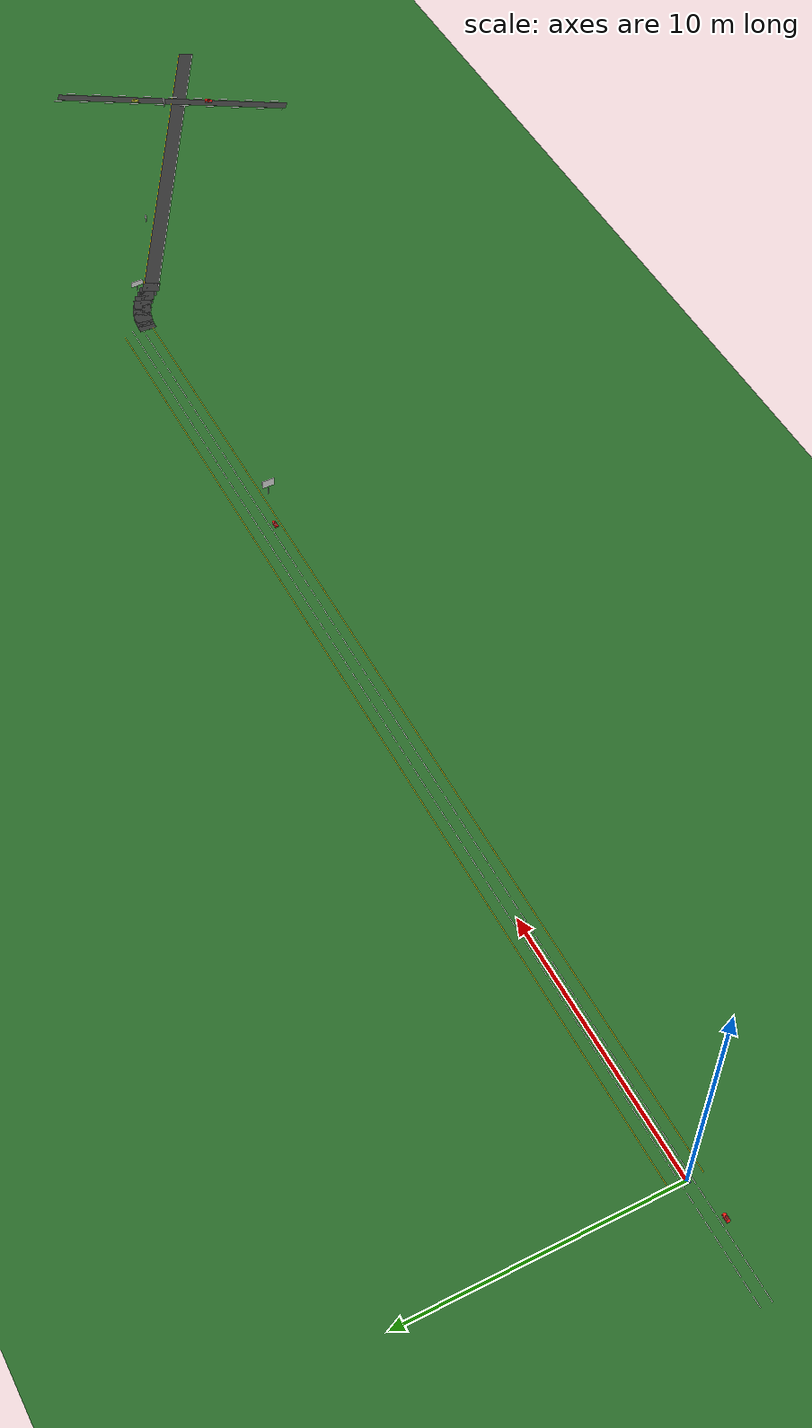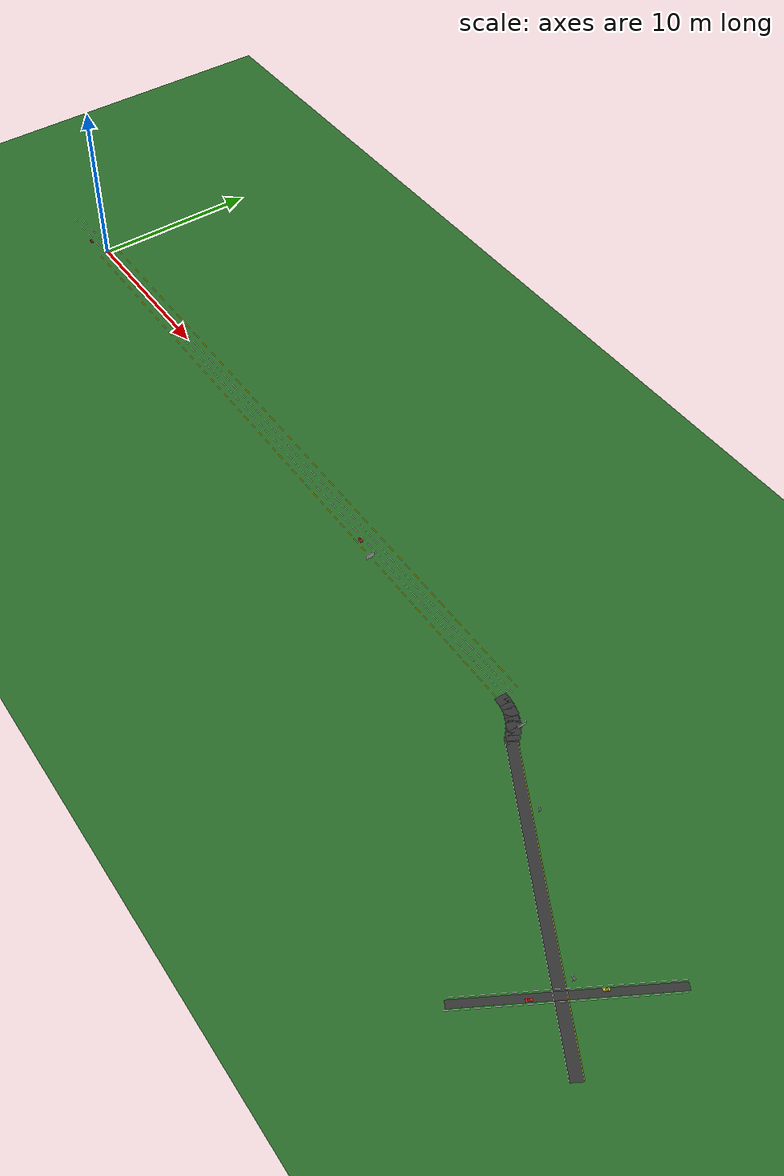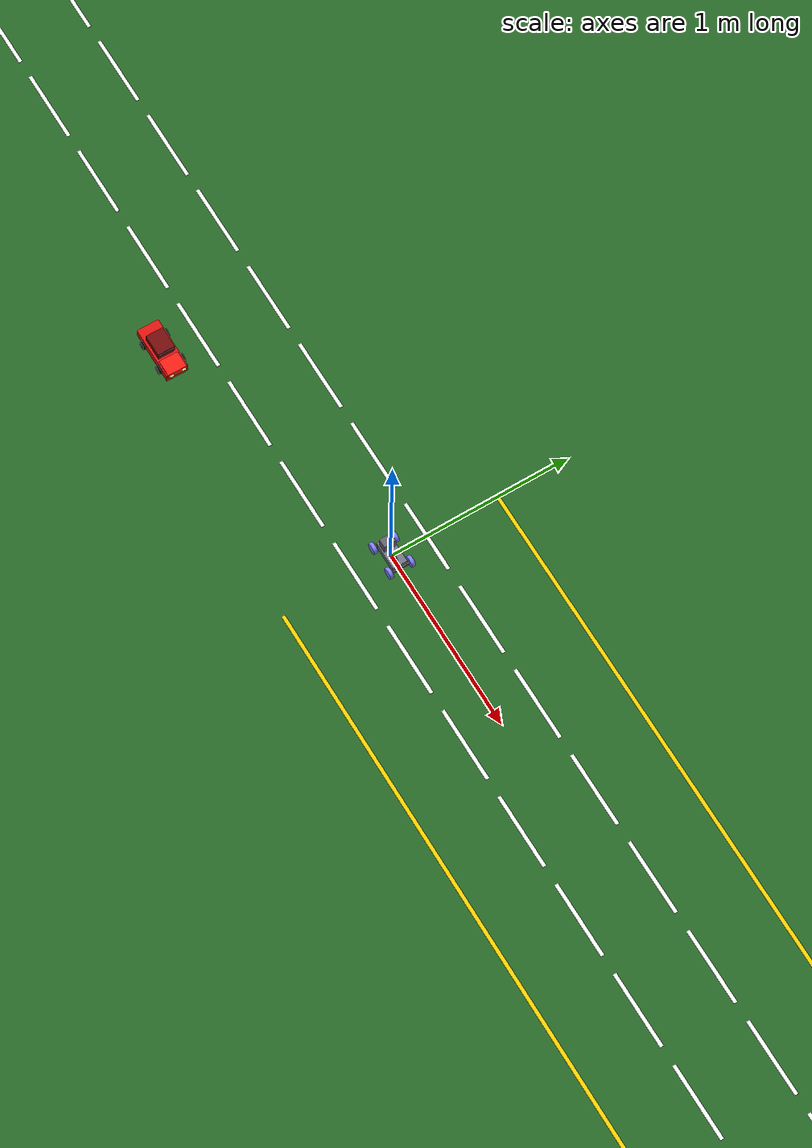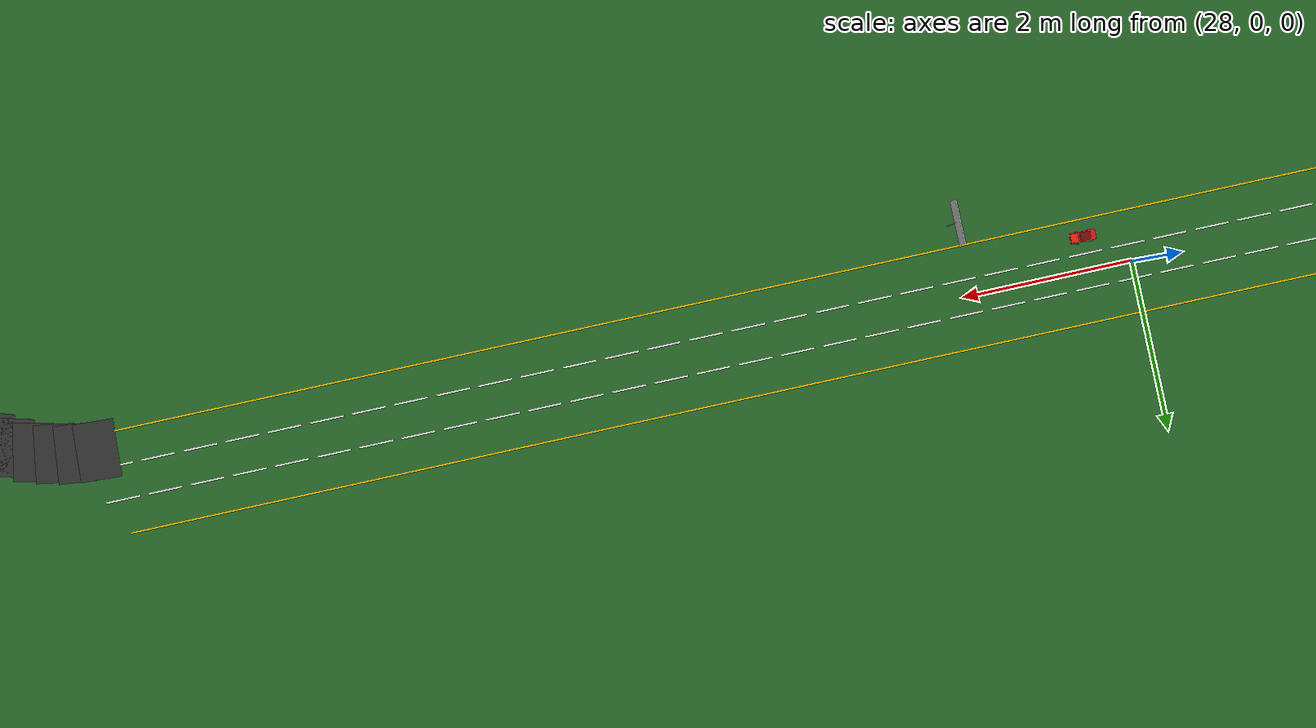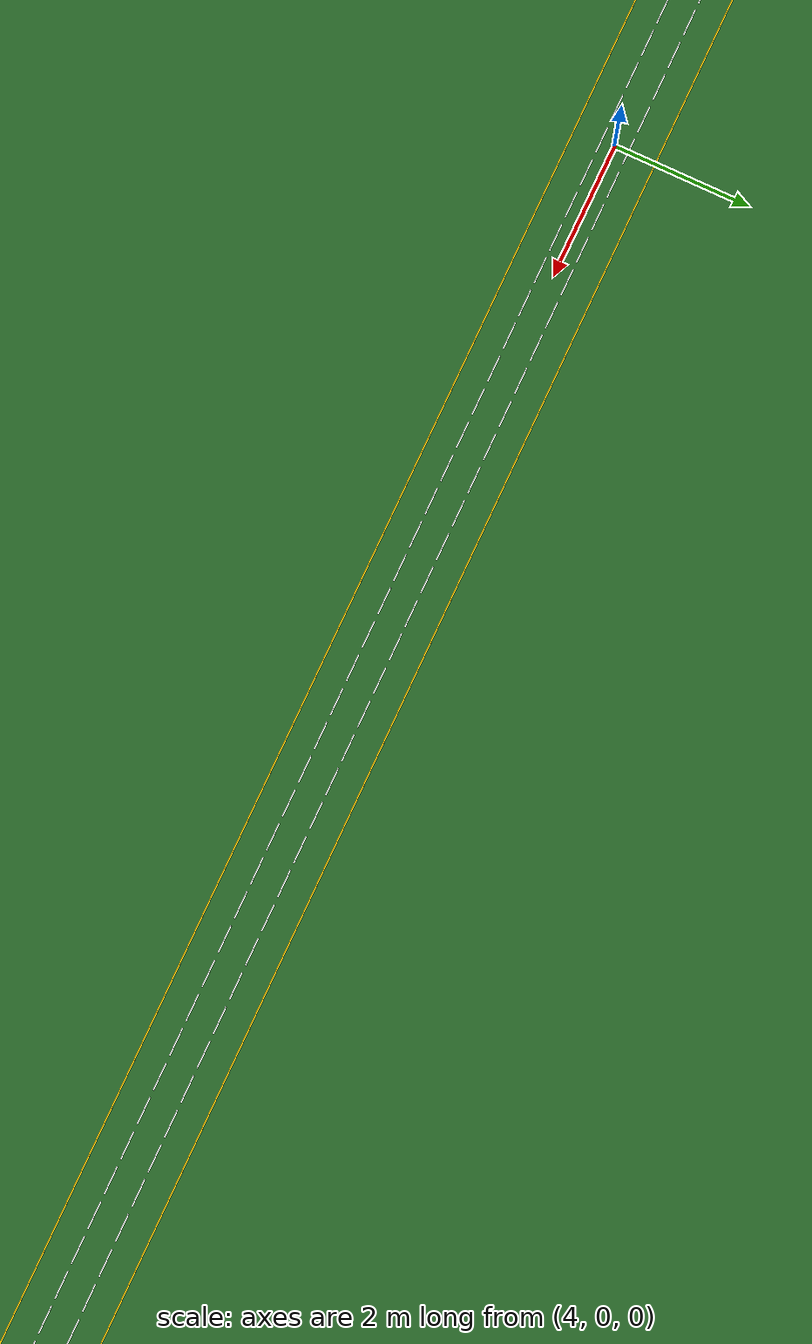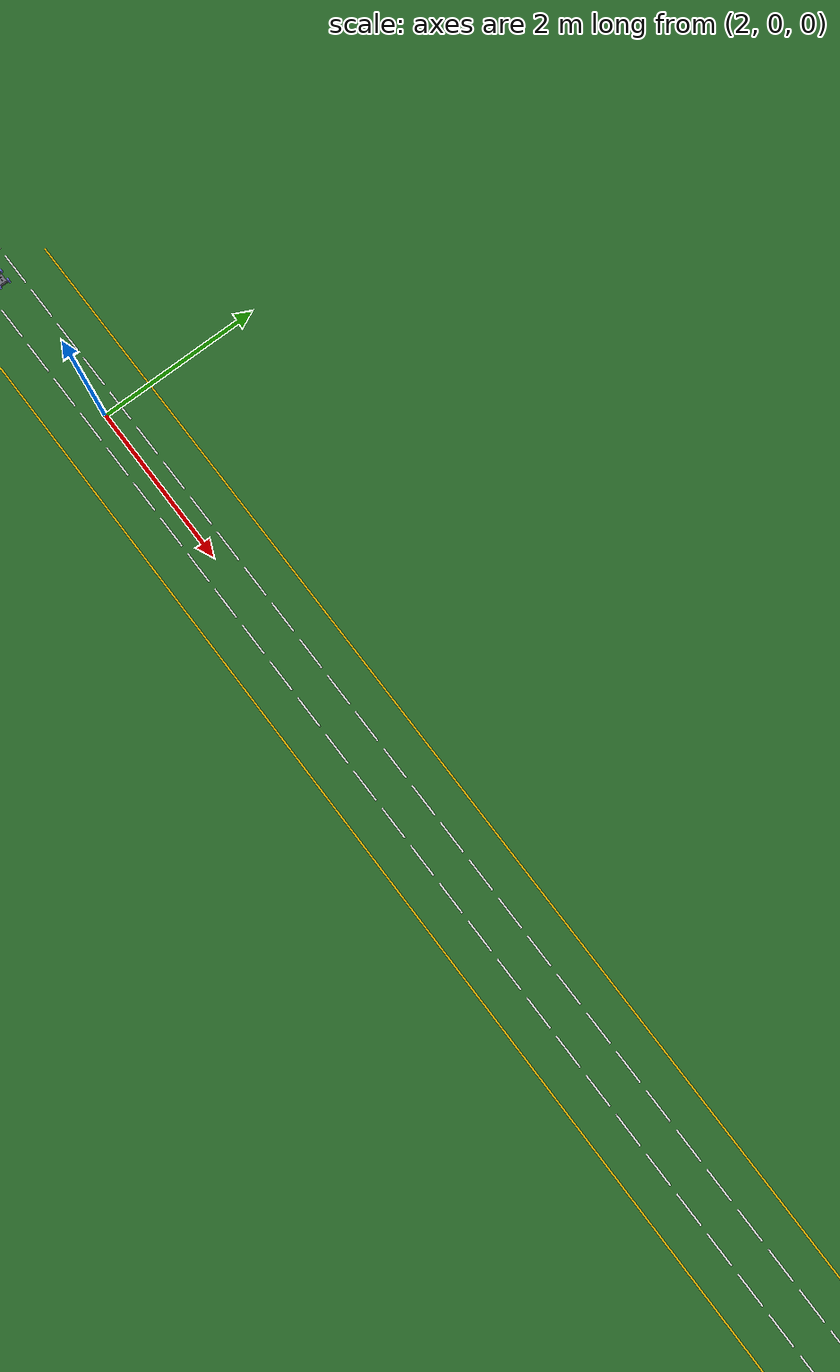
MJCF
<mujoco>
  <compiler autolimits="true"/>

  <!-- Setting to adjust camera/mouse sensitivity to match the car's scale.
       Prevents the massive camera jump on mouse scroll since the initial track was huge. -->
  <statistic extent="3.0" center="0 0 0"/>

  <asset>
      <texture name="grid" type="2d" builtin="checker" width="512" height="512" rgb1=".1 .2 .3" rgb2=".2 .3 .4"/>
      <material name="grid" texture="grid" texrepeat="1 1" texuniform="true" reflectance=".2"/>

    <!-- Sign textures (paths relative to this XML file directory) -->
      <texture name="exit_sign_tex" type="2d" file="exitsign.png"/>
      <material name="exit_sign_mat" texture="exit_sign_tex" texrepeat="1 1" texuniform="true" emission="0.35"/>

      <texture name="lane_change_sign_tex" type="2d" file="lanechange.png"/>
      <material name="lane_change_sign_mat" texture="lane_change_sign_tex" texrepeat="1 1" texuniform="true" emission="0.35"/>

      <texture name="speed_limit_sign_tex" type="2d" file="speed_limit.png"/>
      <material name="speed_limit_sign_mat" texture="speed_limit_sign_tex" texrepeat="1 1" texuniform="true" emission="0.35"/>

      <texture name="stop_sign_tex" type="2d" file="stopsign.png"/>
      <material name="stop_sign_mat" texture="stop_sign_tex" texrepeat="1 1" texuniform="true" emission="0.35"/>
  </asset>

  <default>
    <joint damping=".03" />
    <default class="wheel">
      <geom type="cylinder" size=".03 .01" rgba=".5 .5 1 1"/>
    </default>
    <!-- Steer knuckle joint: larger force range so position actuator can hold angle -->
    <default class="steer">
      <joint type="hinge" axis="0 0 1" range="-0.6 0.6" damping="0.1" actuatorfrcrange="-5 5"/>
    </default>
  </default>

  <worldbody>
    <!-- Wide grassy background for the extended 6 km highway segment. -->
    <geom name="grass" type="plane" pos="30 0 -0.01" size="45 20 .01" rgba="0.15 0.4 0.15 1"/>

    <!-- Straight 6 km, 3-lane road. Scale: 1 MuJoCo meter = 100 real meters; lane centers are y=0.25, y=0.0, y=-0.25. -->
    <geom name="road_asphalt" type="plane" pos="30 0 0" size="45 0.60 .01" rgba="0.2 0.2 0.2 1"/>

    <!-- White dashed lane lines (2cm thick, 1.5m dash length, 1.5m gap) -->
    <geom name="dash_-4.0_L" type="box" pos="-4.0 -0.2 0.002" size="0.2 0.01 0.001" rgba="1 1 1 1" contype="0" conaffinity="0"/>
    <geom name="dash_-4.0_R" type="box" pos="-4.0  0.2 0.002" size="0.2 0.01 0.001" rgba="1 1 1 1" contype="0" conaffinity="0"/>
    <geom name="dash_-3.5_L" type="box" pos="-3.5 -0.2 0.002" size="0.2 0.01 0.001" rgba="1 1 1 1" contype="0" conaffinity="0"/>
    <geom name="dash_-3.5_R" type="box" pos="-3.5  0.2 0.002" size="0.2 0.01 0.001" rgba="1 1 1 1" contype="0" conaffinity="0"/>
    <geom name="dash_-3.0_L" type="box" pos="-3.0 -0.2 0.002" size="0.2 0.01 0.001" rgba="1 1 1 1" contype="0" conaffinity="0"/>
    <geom name="dash_-3.0_R" type="box" pos="-3.0  0.2 0.002" size="0.2 0.01 0.001" rgba="1 1 1 1" contype="0" conaffinity="0"/>
    <geom name="dash_-2.5_L" type="box" pos="-2.5 -0.2 0.002" size="0.2 0.01 0.001" rgba="1 1 1 1" contype="0" conaffinity="0"/>
    <geom name="dash_-2.5_R" type="box" pos="-2.5  0.2 0.002" size="0.2 0.01 0.001" rgba="1 1 1 1" contype="0" conaffinity="0"/>
    <geom name="dash_-2.0_L" type="box" pos="-2.0 -0.2 0.002" size="0.2 0.01 0.001" rgba="1 1 1 1" contype="0" conaffinity="0"/>
    <geom name="dash_-2.0_R" type="box" pos="-2.0  0.2 0.002" size="0.2 0.01 0.001" rgba="1 1 1 1" contype="0" conaffinity="0"/>
    <geom name="dash_-1.5_L" type="box" pos="-1.5 -0.2 0.002" size="0.2 0.01 0.001" rgba="1 1 1 1" contype="0" conaffinity="0"/>
    <geom name="dash_-1.5_R" type="box" pos="-1.5  0.2 0.002" size="0.2 0.01 0.001" rgba="1 1 1 1" contype="0" conaffinity="0"/>
    <geom name="dash_-1.0_L" type="box" pos="-1.0 -0.2 0.002" size="0.2 0.01 0.001" rgba="1 1 1 1" contype="0" conaffinity="0"/>
    <geom name="dash_-1.0_R" type="box" pos="-1.0  0.2 0.002" size="0.2 0.01 0.001" rgba="1 1 1 1" contype="0" conaffinity="0"/>
    <geom name="dash_-0.5_L" type="box" pos="-0.5 -0.2 0.002" size="0.2 0.01 0.001" rgba="1 1 1 1" contype="0" conaffinity="0"/>
    <geom name="dash_-0.5_R" type="box" pos="-0.5  0.2 0.002" size="0.2 0.01 0.001" rgba="1 1 1 1" contype="0" conaffinity="0"/>
    <geom name="dash_0.0_L" type="box" pos="0.0 -0.2 0.002" size="0.2 0.01 0.001" rgba="1 1 1 1" contype="0" conaffinity="0"/>
    <geom name="dash_0.0_R" type="box" pos="0.0  0.2 0.002" size="0.2 0.01 0.001" rgba="1 1 1 1" contype="0" conaffinity="0"/>
    <geom name="dash_0.5_L" type="box" pos="0.5 -0.2 0.002" size="0.2 0.01 0.001" rgba="1 1 1 1" contype="0" conaffinity="0"/>
    <geom name="dash_0.5_R" type="box" pos="0.5  0.2 0.002" size="0.2 0.01 0.001" rgba="1 1 1 1" contype="0" conaffinity="0"/>
    <geom name="dash_1.0_L" type="box" pos="1.0 -0.2 0.002" size="0.2 0.01 0.001" rgba="1 1 1 1" contype="0" conaffinity="0"/>
    <geom name="dash_1.0_R" type="box" pos="1.0  0.2 0.002" size="0.2 0.01 0.001" rgba="1 1 1 1" contype="0" conaffinity="0"/>
    <geom name="dash_1.5_L" type="box" pos="1.5 -0.2 0.002" size="0.2 0.01 0.001" rgba="1 1 1 1" contype="0" conaffinity="0"/>
    <geom name="dash_1.5_R" type="box" pos="1.5  0.2 0.002" size="0.2 0.01 0.001" rgba="1 1 1 1" contype="0" conaffinity="0"/>
    <geom name="dash_2.0_L" type="box" pos="2.0 -0.2 0.002" size="0.2 0.01 0.001" rgba="1 1 1 1" contype="0" conaffinity="0"/>
    <geom name="dash_2.0_R" type="box" pos="2.0  0.2 0.002" size="0.2 0.01 0.001" rgba="1 1 1 1" contype="0" conaffinity="0"/>
    <geom name="dash_2.5_L" type="box" pos="2.5 -0.2 0.002" size="0.2 0.01 0.001" rgba="1 1 1 1" contype="0" conaffinity="0"/>
    <geom name="dash_2.5_R" type="box" pos="2.5  0.2 0.002" size="0.2 0.01 0.001" rgba="1 1 1 1" contype="0" conaffinity="0"/>
    <geom name="dash_3.0_L" type="box" pos="3.0 -0.2 0.002" size="0.2 0.01 0.001" rgba="1 1 1 1" contype="0" conaffinity="0"/>
    <geom name="dash_3.0_R" type="box" pos="3.0  0.2 0.002" size="0.2 0.01 0.001" rgba="1 1 1 1" contype="0" conaffinity="0"/>
    <geom name="dash_3.5_L" type="box" pos="3.5 -0.2 0.002" size="0.2 0.01 0.001" rgba="1 1 1 1" contype="0" conaffinity="0"/>
    <geom name="dash_3.5_R" type="box" pos="3.5  0.2 0.002" size="0.2 0.01 0.001" rgba="1 1 1 1" contype="0" conaffinity="0"/>
    <geom name="dash_4.0_L" type="box" pos="4.0 -0.2 0.002" size="0.2 0.01 0.001" rgba="1 1 1 1" contype="0" conaffinity="0"/>
    <geom name="dash_4.0_R" type="box" pos="4.0  0.2 0.002" size="0.2 0.01 0.001" rgba="1 1 1 1" contype="0" conaffinity="0"/>
    <geom name="dash_4.5_L" type="box" pos="4.5 -0.2 0.002" size="0.2 0.01 0.001" rgba="1 1 1 1" contype="0" conaffinity="0"/>
    <geom name="dash_4.5_R" type="box" pos="4.5  0.2 0.002" size="0.2 0.01 0.001" rgba="1 1 1 1" contype="0" conaffinity="0"/>
    <geom name="dash_5.0_L" type="box" pos="5.0 -0.2 0.002" size="0.2 0.01 0.001" rgba="1 1 1 1" contype="0" conaffinity="0"/>
    <geom name="dash_5.0_R" type="box" pos="5.0  0.2 0.002" size="0.2 0.01 0.001" rgba="1 1 1 1" contype="0" conaffinity="0"/>
    <geom name="dash_5.5_L" type="box" pos="5.5 -0.2 0.002" size="0.2 0.01 0.001" rgba="1 1 1 1" contype="0" conaffinity="0"/>
    <geom name="dash_5.5_R" type="box" pos="5.5  0.2 0.002" size="0.2 0.01 0.001" rgba="1 1 1 1" contype="0" conaffinity="0"/>
    <geom name="dash_6.0_L" type="box" pos="6.0 -0.2 0.002" size="0.2 0.01 0.001" rgba="1 1 1 1" contype="0" conaffinity="0"/>
    <geom name="dash_6.0_R" type="box" pos="6.0  0.2 0.002" size="0.2 0.01 0.001" rgba="1 1 1 1" contype="0" conaffinity="0"/>
    <geom name="dash_6.5_L" type="box" pos="6.5 -0.2 0.002" size="0.2 0.01 0.001" rgba="1 1 1 1" contype="0" conaffinity="0"/>
    <geom name="dash_6.5_R" type="box" pos="6.5  0.2 0.002" size="0.2 0.01 0.001" rgba="1 1 1 1" contype="0" conaffinity="0"/>
    <geom name="dash_7.0_L" type="box" pos="7.0 -0.2 0.002" size="0.2 0.01 0.001" rgba="1 1 1 1" contype="0" conaffinity="0"/>
    <geom name="dash_7.0_R" type="box" pos="7.0  0.2 0.002" size="0.2 0.01 0.001" rgba="1 1 1 1" contype="0" conaffinity="0"/>
    <geom name="dash_7.5_L" type="box" pos="7.5 -0.2 0.002" size="0.2 0.01 0.001" rgba="1 1 1 1" contype="0" conaffinity="0"/>
    <geom name="dash_7.5_R" type="box" pos="7.5  0.2 0.002" size="0.2 0.01 0.001" rgba="1 1 1 1" contype="0" conaffinity="0"/>
    <geom name="dash_8.0_L" type="box" pos="8.0 -0.2 0.002" size="0.2 0.01 0.001" rgba="1 1 1 1" contype="0" conaffinity="0"/>
    <geom name="dash_8.0_R" type="box" pos="8.0  0.2 0.002" size="0.2 0.01 0.001" rgba="1 1 1 1" contype="0" conaffinity="0"/>
    <geom name="dash_8.5_L" type="box" pos="8.5 -0.2 0.002" size="0.2 0.01 0.001" rgba="1 1 1 1" contype="0" conaffinity="0"/>
    <geom name="dash_8.5_R" type="box" pos="8.5  0.2 0.002" size="0.2 0.01 0.001" rgba="1 1 1 1" contype="0" conaffinity="0"/>
    <geom name="dash_9.0_L" type="box" pos="9.0 -0.2 0.002" size="0.2 0.01 0.001" rgba="1 1 1 1" contype="0" conaffinity="0"/>
    <geom name="dash_9.0_R" type="box" pos="9.0  0.2 0.002" size="0.2 0.01 0.001" rgba="1 1 1 1" contype="0" conaffinity="0"/>
    <geom name="dash_9.5_L" type="box" pos="9.5 -0.2 0.002" size="0.2 0.01 0.001" rgba="1 1 1 1" contype="0" conaffinity="0"/>
    <geom name="dash_9.5_R" type="box" pos="9.5  0.2 0.002" size="0.2 0.01 0.001" rgba="1 1 1 1" contype="0" conaffinity="0"/>
    <geom name="dash_10.0_L" type="box" pos="10.0 -0.2 0.002" size="0.2 0.01 0.001" rgba="1 1 1 1" contype="0" conaffinity="0"/>
    <geom name="dash_10.0_R" type="box" pos="10.0  0.2 0.002" size="0.2 0.01 0.001" rgba="1 1 1 1" contype="0" conaffinity="0"/>
    <geom name="dash_10.5_L" type="box" pos="10.5 -0.2 0.002" size="0.2 0.01 0.001" rgba="1 1 1 1" contype="0" conaffinity="0"/>
    <geom name="dash_10.5_R" type="box" pos="10.5  0.2 0.002" size="0.2 0.01 0.001" rgba="1 1 1 1" contype="0" conaffinity="0"/>
    <geom name="dash_11.0_L" type="box" pos="11.0 -0.2 0.002" size="0.2 0.01 0.001" rgba="1 1 1 1" contype="0" conaffinity="0"/>
    <geom name="dash_11.0_R" type="box" pos="11.0  0.2 0.002" size="0.2 0.01 0.001" rgba="1 1 1 1" contype="0" conaffinity="0"/>
    <geom name="dash_11.5_L" type="box" pos="11.5 -0.2 0.002" size="0.2 0.01 0.001" rgba="1 1 1 1" contype="0" conaffinity="0"/>
    <geom name="dash_11.5_R" type="box" pos="11.5  0.2 0.002" size="0.2 0.01 0.001" rgba="1 1 1 1" contype="0" conaffinity="0"/>
    <geom name="dash_12.0_L" type="box" pos="12.0 -0.2 0.002" size="0.2 0.01 0.001" rgba="1 1 1 1" contype="0" conaffinity="0"/>
    <geom name="dash_12.0_R" type="box" pos="12.0  0.2 0.002" size="0.2 0.01 0.001" rgba="1 1 1 1" contype="0" conaffinity="0"/>
    <geom name="dash_12.5_L" type="box" pos="12.5 -0.2 0.002" size="0.2 0.01 0.001" rgba="1 1 1 1" contype="0" conaffinity="0"/>
    <geom name="dash_12.5_R" type="box" pos="12.5  0.2 0.002" size="0.2 0.01 0.001" rgba="1 1 1 1" contype="0" conaffinity="0"/>
    <geom name="dash_13.0_L" type="box" pos="13.0 -0.2 0.002" size="0.2 0.01 0.001" rgba="1 1 1 1" contype="0" conaffinity="0"/>
    <geom name="dash_13.0_R" type="box" pos="13.0  0.2 0.002" size="0.2 0.01 0.001" rgba="1 1 1 1" contype="0" conaffinity="0"/>
    <geom name="dash_13.5_L" type="box" pos="13.5 -0.2 0.002" size="0.2 0.01 0.001" rgba="1 1 1 1" contype="0" conaffinity="0"/>
    <geom name="dash_13.5_R" type="box" pos="13.5  0.2 0.002" size="0.2 0.01 0.001" rgba="1 1 1 1" contype="0" conaffinity="0"/>
    <geom name="dash_14.0_L" type="box" pos="14.0 -0.2 0.002" size="0.2 0.01 0.001" rgba="1 1 1 1" contype="0" conaffinity="0"/>
    <geom name="dash_14.0_R" type="box" pos="14.0  0.2 0.002" size="0.2 0.01 0.001" rgba="1 1 1 1" contype="0" conaffinity="0"/>
    <geom name="dash_14.5_L" type="box" pos="14.5 -0.2 0.002" size="0.2 0.01 0.001" rgba="1 1 1 1" contype="0" conaffinity="0"/>
    <geom name="dash_14.5_R" type="box" pos="14.5  0.2 0.002" size="0.2 0.01 0.001" rgba="1 1 1 1" contype="0" conaffinity="0"/>
    <geom name="dash_15.0_L" type="box" pos="15.0 -0.2 0.002" size="0.2 0.01 0.001" rgba="1 1 1 1" contype="0" conaffinity="0"/>
    <geom name="dash_15.0_R" type="box" pos="15.0  0.2 0.002" size="0.2 0.01 0.001" rgba="1 1 1 1" contype="0" conaffinity="0"/>
    <geom name="dash_15.5_L" type="box" pos="15.5 -0.2 0.002" size="0.2 0.01 0.001" rgba="1 1 1 1" contype="0" conaffinity="0"/>
    <geom name="dash_15.5_R" type="box" pos="15.5  0.2 0.002" size="0.2 0.01 0.001" rgba="1 1 1 1" contype="0" conaffinity="0"/>
    <geom name="dash_16.0_L" type="box" pos="16.0 -0.2 0.002" size="0.2 0.01 0.001" rgba="1 1 1 1" contype="0" conaffinity="0"/>
    <geom name="dash_16.0_R" type="box" pos="16.0  0.2 0.002" size="0.2 0.01 0.001" rgba="1 1 1 1" contype="0" conaffinity="0"/>
    <geom name="dash_16.5_L" type="box" pos="16.5 -0.2 0.002" size="0.2 0.01 0.001" rgba="1 1 1 1" contype="0" conaffinity="0"/>
    <geom name="dash_16.5_R" type="box" pos="16.5  0.2 0.002" size="0.2 0.01 0.001" rgba="1 1 1 1" contype="0" conaffinity="0"/>
    <geom name="dash_17.0_L" type="box" pos="17.0 -0.2 0.002" size="0.2 0.01 0.001" rgba="1 1 1 1" contype="0" conaffinity="0"/>
    <geom name="dash_17.0_R" type="box" pos="17.0  0.2 0.002" size="0.2 0.01 0.001" rgba="1 1 1 1" contype="0" conaffinity="0"/>
    <geom name="dash_17.5_L" type="box" pos="17.5 -0.2 0.002" size="0.2 0.01 0.001" rgba="1 1 1 1" contype="0" conaffinity="0"/>
    <geom name="dash_17.5_R" type="box" pos="17.5  0.2 0.002" size="0.2 0.01 0.001" rgba="1 1 1 1" contype="0" conaffinity="0"/>
    <geom name="dash_18.0_L" type="box" pos="18.0 -0.2 0.002" size="0.2 0.01 0.001" rgba="1 1 1 1" contype="0" conaffinity="0"/>
    <geom name="dash_18.0_R" type="box" pos="18.0  0.2 0.002" size="0.2 0.01 0.001" rgba="1 1 1 1" contype="0" conaffinity="0"/>
    <geom name="dash_18.5_L" type="box" pos="18.5 -0.2 0.002" size="0.2 0.01 0.001" rgba="1 1 1 1" contype="0" conaffinity="0"/>
    <geom name="dash_18.5_R" type="box" pos="18.5  0.2 0.002" size="0.2 0.01 0.001" rgba="1 1 1 1" contype="0" conaffinity="0"/>
    <geom name="dash_19.0_L" type="box" pos="19.0 -0.2 0.002" size="0.2 0.01 0.001" rgba="1 1 1 1" contype="0" conaffinity="0"/>
    <geom name="dash_19.0_R" type="box" pos="19.0  0.2 0.002" size="0.2 0.01 0.001" rgba="1 1 1 1" contype="0" conaffinity="0"/>
    <geom name="dash_19.5_L" type="box" pos="19.5 -0.2 0.002" size="0.2 0.01 0.001" rgba="1 1 1 1" contype="0" conaffinity="0"/>
    <geom name="dash_19.5_R" type="box" pos="19.5  0.2 0.002" size="0.2 0.01 0.001" rgba="1 1 1 1" contype="0" conaffinity="0"/>
    <geom name="dash_20.0_L" type="box" pos="20.0 -0.2 0.002" size="0.2 0.01 0.001" rgba="1 1 1 1" contype="0" conaffinity="0"/>
    <geom name="dash_20.0_R" type="box" pos="20.0  0.2 0.002" size="0.2 0.01 0.001" rgba="1 1 1 1" contype="0" conaffinity="0"/>
    <geom name="dash_20.5_L" type="box" pos="20.5 -0.2 0.002" size="0.2 0.01 0.001" rgba="1 1 1 1" contype="0" conaffinity="0"/>
    <geom name="dash_20.5_R" type="box" pos="20.5  0.2 0.002" size="0.2 0.01 0.001" rgba="1 1 1 1" contype="0" conaffinity="0"/>
    <geom name="dash_21.0_L" type="box" pos="21.0 -0.2 0.002" size="0.2 0.01 0.001" rgba="1 1 1 1" contype="0" conaffinity="0"/>
    <geom name="dash_21.0_R" type="box" pos="21.0  0.2 0.002" size="0.2 0.01 0.001" rgba="1 1 1 1" contype="0" conaffinity="0"/>
    <geom name="dash_21.5_L" type="box" pos="21.5 -0.2 0.002" size="0.2 0.01 0.001" rgba="1 1 1 1" contype="0" conaffinity="0"/>
    <geom name="dash_21.5_R" type="box" pos="21.5  0.2 0.002" size="0.2 0.01 0.001" rgba="1 1 1 1" contype="0" conaffinity="0"/>
    <geom name="dash_22.0_L" type="box" pos="22.0 -0.2 0.002" size="0.2 0.01 0.001" rgba="1 1 1 1" contype="0" conaffinity="0"/>
    <geom name="dash_22.0_R" type="box" pos="22.0  0.2 0.002" size="0.2 0.01 0.001" rgba="1 1 1 1" contype="0" conaffinity="0"/>
    <geom name="dash_22.5_L" type="box" pos="22.5 -0.2 0.002" size="0.2 0.01 0.001" rgba="1 1 1 1" contype="0" conaffinity="0"/>
    <geom name="dash_22.5_R" type="box" pos="22.5  0.2 0.002" size="0.2 0.01 0.001" rgba="1 1 1 1" contype="0" conaffinity="0"/>
    <geom name="dash_23.0_L" type="box" pos="23.0 -0.2 0.002" size="0.2 0.01 0.001" rgba="1 1 1 1" contype="0" conaffinity="0"/>
    <geom name="dash_23.0_R" type="box" pos="23.0  0.2 0.002" size="0.2 0.01 0.001" rgba="1 1 1 1" contype="0" conaffinity="0"/>
    <geom name="dash_23.5_L" type="box" pos="23.5 -0.2 0.002" size="0.2 0.01 0.001" rgba="1 1 1 1" contype="0" conaffinity="0"/>
    <geom name="dash_23.5_R" type="box" pos="23.5  0.2 0.002" size="0.2 0.01 0.001" rgba="1 1 1 1" contype="0" conaffinity="0"/>
    <geom name="dash_24.0_L" type="box" pos="24.0 -0.2 0.002" size="0.2 0.01 0.001" rgba="1 1 1 1" contype="0" conaffinity="0"/>
    <geom name="dash_24.0_R" type="box" pos="24.0  0.2 0.002" size="0.2 0.01 0.001" rgba="1 1 1 1" contype="0" conaffinity="0"/>
    <geom name="dash_24.5_L" type="box" pos="24.5 -0.2 0.002" size="0.2 0.01 0.001" rgba="1 1 1 1" contype="0" conaffinity="0"/>
    <geom name="dash_24.5_R" type="box" pos="24.5  0.2 0.002" size="0.2 0.01 0.001" rgba="1 1 1 1" contype="0" conaffinity="0"/>
    <geom name="dash_25.0_L" type="box" pos="25.0 -0.2 0.002" size="0.2 0.01 0.001" rgba="1 1 1 1" contype="0" conaffinity="0"/>
    <geom name="dash_25.0_R" type="box" pos="25.0  0.2 0.002" size="0.2 0.01 0.001" rgba="1 1 1 1" contype="0" conaffinity="0"/>
    <geom name="dash_25.5_L" type="box" pos="25.5 -0.2 0.002" size="0.2 0.01 0.001" rgba="1 1 1 1" contype="0" conaffinity="0"/>
    <geom name="dash_25.5_R" type="box" pos="25.5  0.2 0.002" size="0.2 0.01 0.001" rgba="1 1 1 1" contype="0" conaffinity="0"/>
    <geom name="dash_26.0_L" type="box" pos="26.0 -0.2 0.002" size="0.2 0.01 0.001" rgba="1 1 1 1" contype="0" conaffinity="0"/>
    <geom name="dash_26.0_R" type="box" pos="26.0  0.2 0.002" size="0.2 0.01 0.001" rgba="1 1 1 1" contype="0" conaffinity="0"/>
    <geom name="dash_26.5_L" type="box" pos="26.5 -0.2 0.002" size="0.2 0.01 0.001" rgba="1 1 1 1" contype="0" conaffinity="0"/>
    <geom name="dash_26.5_R" type="box" pos="26.5  0.2 0.002" size="0.2 0.01 0.001" rgba="1 1 1 1" contype="0" conaffinity="0"/>
    <geom name="dash_27.0_L" type="box" pos="27.0 -0.2 0.002" size="0.2 0.01 0.001" rgba="1 1 1 1" contype="0" conaffinity="0"/>
    <geom name="dash_27.0_R" type="box" pos="27.0  0.2 0.002" size="0.2 0.01 0.001" rgba="1 1 1 1" contype="0" conaffinity="0"/>
    <geom name="dash_27.5_L" type="box" pos="27.5 -0.2 0.002" size="0.2 0.01 0.001" rgba="1 1 1 1" contype="0" conaffinity="0"/>
    <geom name="dash_27.5_R" type="box" pos="27.5  0.2 0.002" size="0.2 0.01 0.001" rgba="1 1 1 1" contype="0" conaffinity="0"/>
    <geom name="dash_28.0_L" type="box" pos="28.0 -0.2 0.002" size="0.2 0.01 0.001" rgba="1 1 1 1" contype="0" conaffinity="0"/>
    <geom name="dash_28.0_R" type="box" pos="28.0  0.2 0.002" size="0.2 0.01 0.001" rgba="1 1 1 1" contype="0" conaffinity="0"/>
    <geom name="dash_28.5_L" type="box" pos="28.5 -0.2 0.002" size="0.2 0.01 0.001" rgba="1 1 1 1" contype="0" conaffinity="0"/>
    <geom name="dash_28.5_R" type="box" pos="28.5  0.2 0.002" size="0.2 0.01 0.001" rgba="1 1 1 1" contype="0" conaffinity="0"/>
    <geom name="dash_29.0_L" type="box" pos="29.0 -0.2 0.002" size="0.2 0.01 0.001" rgba="1 1 1 1" contype="0" conaffinity="0"/>
    <geom name="dash_29.0_R" type="box" pos="29.0  0.2 0.002" size="0.2 0.01 0.001" rgba="1 1 1 1" contype="0" conaffinity="0"/>
    <geom name="dash_29.5_L" type="box" pos="29.5 -0.2 0.002" size="0.2 0.01 0.001" rgba="1 1 1 1" contype="0" conaffinity="0"/>
    <geom name="dash_29.5_R" type="box" pos="29.5  0.2 0.002" size="0.2 0.01 0.001" rgba="1 1 1 1" contype="0" conaffinity="0"/>
    <geom name="dash_30.0_L" type="box" pos="30.0 -0.2 0.002" size="0.2 0.01 0.001" rgba="1 1 1 1" contype="0" conaffinity="0"/>
    <geom name="dash_30.0_R" type="box" pos="30.0  0.2 0.002" size="0.2 0.01 0.001" rgba="1 1 1 1" contype="0" conaffinity="0"/>
    <geom name="dash_30.5_L" type="box" pos="30.5 -0.2 0.002" size="0.2 0.01 0.001" rgba="1 1 1 1" contype="0" conaffinity="0"/>
    <geom name="dash_30.5_R" type="box" pos="30.5  0.2 0.002" size="0.2 0.01 0.001" rgba="1 1 1 1" contype="0" conaffinity="0"/>
    <geom name="dash_31.0_L" type="box" pos="31.0 -0.2 0.002" size="0.2 0.01 0.001" rgba="1 1 1 1" contype="0" conaffinity="0"/>
    <geom name="dash_31.0_R" type="box" pos="31.0  0.2 0.002" size="0.2 0.01 0.001" rgba="1 1 1 1" contype="0" conaffinity="0"/>
    <geom name="dash_31.5_L" type="box" pos="31.5 -0.2 0.002" size="0.2 0.01 0.001" rgba="1 1 1 1" contype="0" conaffinity="0"/>
    <geom name="dash_31.5_R" type="box" pos="31.5  0.2 0.002" size="0.2 0.01 0.001" rgba="1 1 1 1" contype="0" conaffinity="0"/>
    <geom name="dash_32.0_L" type="box" pos="32.0 -0.2 0.002" size="0.2 0.01 0.001" rgba="1 1 1 1" contype="0" conaffinity="0"/>
    <geom name="dash_32.0_R" type="box" pos="32.0  0.2 0.002" size="0.2 0.01 0.001" rgba="1 1 1 1" contype="0" conaffinity="0"/>
    <geom name="dash_32.5_L" type="box" pos="32.5 -0.2 0.002" size="0.2 0.01 0.001" rgba="1 1 1 1" contype="0" conaffinity="0"/>
    <geom name="dash_32.5_R" type="box" pos="32.5  0.2 0.002" size="0.2 0.01 0.001" rgba="1 1 1 1" contype="0" conaffinity="0"/>
    <geom name="dash_33.0_L" type="box" pos="33.0 -0.2 0.002" size="0.2 0.01 0.001" rgba="1 1 1 1" contype="0" conaffinity="0"/>
    <geom name="dash_33.0_R" type="box" pos="33.0  0.2 0.002" size="0.2 0.01 0.001" rgba="1 1 1 1" contype="0" conaffinity="0"/>
    <geom name="dash_33.5_L" type="box" pos="33.5 -0.2 0.002" size="0.2 0.01 0.001" rgba="1 1 1 1" contype="0" conaffinity="0"/>
    <geom name="dash_33.5_R" type="box" pos="33.5  0.2 0.002" size="0.2 0.01 0.001" rgba="1 1 1 1" contype="0" conaffinity="0"/>
    <geom name="dash_34.0_L" type="box" pos="34.0 -0.2 0.002" size="0.2 0.01 0.001" rgba="1 1 1 1" contype="0" conaffinity="0"/>
    <geom name="dash_34.0_R" type="box" pos="34.0  0.2 0.002" size="0.2 0.01 0.001" rgba="1 1 1 1" contype="0" conaffinity="0"/>
    <geom name="dash_34.5_L" type="box" pos="34.5 -0.2 0.002" size="0.2 0.01 0.001" rgba="1 1 1 1" contype="0" conaffinity="0"/>
    <geom name="dash_34.5_R" type="box" pos="34.5  0.2 0.002" size="0.2 0.01 0.001" rgba="1 1 1 1" contype="0" conaffinity="0"/>
    <geom name="dash_35.0_L" type="box" pos="35.0 -0.2 0.002" size="0.2 0.01 0.001" rgba="1 1 1 1" contype="0" conaffinity="0"/>
    <geom name="dash_35.0_R" type="box" pos="35.0  0.2 0.002" size="0.2 0.01 0.001" rgba="1 1 1 1" contype="0" conaffinity="0"/>
    <geom name="dash_35.5_L" type="box" pos="35.5 -0.2 0.002" size="0.2 0.01 0.001" rgba="1 1 1 1" contype="0" conaffinity="0"/>
    <geom name="dash_35.5_R" type="box" pos="35.5  0.2 0.002" size="0.2 0.01 0.001" rgba="1 1 1 1" contype="0" conaffinity="0"/>
    <geom name="dash_36.0_L" type="box" pos="36.0 -0.2 0.002" size="0.2 0.01 0.001" rgba="1 1 1 1" contype="0" conaffinity="0"/>
    <geom name="dash_36.0_R" type="box" pos="36.0  0.2 0.002" size="0.2 0.01 0.001" rgba="1 1 1 1" contype="0" conaffinity="0"/>
    <geom name="dash_36.5_L" type="box" pos="36.5 -0.2 0.002" size="0.2 0.01 0.001" rgba="1 1 1 1" contype="0" conaffinity="0"/>
    <geom name="dash_36.5_R" type="box" pos="36.5  0.2 0.002" size="0.2 0.01 0.001" rgba="1 1 1 1" contype="0" conaffinity="0"/>
    <geom name="dash_37.0_L" type="box" pos="37.0 -0.2 0.002" size="0.2 0.01 0.001" rgba="1 1 1 1" contype="0" conaffinity="0"/>
    <geom name="dash_37.0_R" type="box" pos="37.0  0.2 0.002" size="0.2 0.01 0.001" rgba="1 1 1 1" contype="0" conaffinity="0"/>
    <geom name="dash_37.5_L" type="box" pos="37.5 -0.2 0.002" size="0.2 0.01 0.001" rgba="1 1 1 1" contype="0" conaffinity="0"/>
    <geom name="dash_37.5_R" type="box" pos="37.5  0.2 0.002" size="0.2 0.01 0.001" rgba="1 1 1 1" contype="0" conaffinity="0"/>
    <geom name="dash_38.0_L" type="box" pos="38.0 -0.2 0.002" size="0.2 0.01 0.001" rgba="1 1 1 1" contype="0" conaffinity="0"/>
    <geom name="dash_38.0_R" type="box" pos="38.0  0.2 0.002" size="0.2 0.01 0.001" rgba="1 1 1 1" contype="0" conaffinity="0"/>
    <geom name="dash_38.5_L" type="box" pos="38.5 -0.2 0.002" size="0.2 0.01 0.001" rgba="1 1 1 1" contype="0" conaffinity="0"/>
    <geom name="dash_38.5_R" type="box" pos="38.5  0.2 0.002" size="0.2 0.01 0.001" rgba="1 1 1 1" contype="0" conaffinity="0"/>
    <geom name="dash_39.0_L" type="box" pos="39.0 -0.2 0.002" size="0.2 0.01 0.001" rgba="1 1 1 1" contype="0" conaffinity="0"/>
    <geom name="dash_39.0_R" type="box" pos="39.0  0.2 0.002" size="0.2 0.01 0.001" rgba="1 1 1 1" contype="0" conaffinity="0"/>
    <geom name="dash_39.5_L" type="box" pos="39.5 -0.2 0.002" size="0.2 0.01 0.001" rgba="1 1 1 1" contype="0" conaffinity="0"/>
    <geom name="dash_39.5_R" type="box" pos="39.5  0.2 0.002" size="0.2 0.01 0.001" rgba="1 1 1 1" contype="0" conaffinity="0"/>
    <geom name="dash_40.0_L" type="box" pos="40.0 -0.2 0.002" size="0.2 0.01 0.001" rgba="1 1 1 1" contype="0" conaffinity="0"/>
    <geom name="dash_40.0_R" type="box" pos="40.0  0.2 0.002" size="0.2 0.01 0.001" rgba="1 1 1 1" contype="0" conaffinity="0"/>

    <!-- Yellow edge lines (matched to road width and 4 km length) -->
    <geom name="edge_line_L" type="box" pos="20 -0.60 0.002" size="20 0.01 0.001" rgba="1 0.8 0 1" contype="0" conaffinity="0"/>
    <geom name="edge_line_R" type="box" pos="20  0.60 0.002" size="20 0.01 0.001" rgba="1 0.8 0 1" contype="0" conaffinity="0"/>

      <!-- Red car passing by in the right lane before lane-change sign -->
      <body name="passing_red_car" pos="28.5 -0.40 0.023">
      <geom name="passing_red_car_body" type="box" pos="0 0 0.015"
            size="0.145 0.060 0.028" rgba="0.86 0.08 0.06 1"/>
      <geom name="passing_red_car_nose" type="box" pos="0.105 0 0.033"
            size="0.045 0.052 0.018" rgba="0.95 0.12 0.08 1"
            contype="0" conaffinity="0"/>
      <geom name="passing_red_car_cabin" type="box" pos="-0.015 0 0.060"
            size="0.060 0.047 0.028" rgba="0.45 0.04 0.04 1"
            contype="0" conaffinity="0"/>
      <geom name="passing_red_car_windshield" type="box" pos="0.030 0 0.082"
            size="0.020 0.040 0.003" rgba="0.08 0.11 0.14 1"
            contype="0" conaffinity="0"/>
      <geom name="passing_red_car_rear_window" type="box" pos="-0.055 0 0.082"
            size="0.018 0.038 0.003" rgba="0.08 0.11 0.14 1"
            contype="0" conaffinity="0"/>
      <geom name="passing_red_car_front_light_l" type="box" pos="0.152 0.034 0.031"
            size="0.006 0.010 0.006" rgba="1.0 0.90 0.45 1"
            contype="0" conaffinity="0"/>
      <geom name="passing_red_car_front_light_r" type="box" pos="0.152 -0.034 0.031"
            size="0.006 0.010 0.006" rgba="1.0 0.90 0.45 1"
            contype="0" conaffinity="0"/>
      <geom name="passing_red_car_wheel_fl" type="cylinder" pos="0.075 0.064 0.000"
            size="0.023 0.010" zaxis="0 1 0" rgba="0.02 0.02 0.025 1"
            contype="0" conaffinity="0"/>
      <geom name="passing_red_car_wheel_fr" type="cylinder" pos="0.075 -0.064 0.000"
            size="0.023 0.010" zaxis="0 1 0" rgba="0.02 0.02 0.025 1"
            contype="0" conaffinity="0"/>
      <geom name="passing_red_car_wheel_rl" type="cylinder" pos="-0.080 0.064 0.000"
            size="0.023 0.010" zaxis="0 1 0" rgba="0.02 0.02 0.025 1"
            contype="0" conaffinity="0"/>
      <geom name="passing_red_car_wheel_rr" type="cylinder" pos="-0.080 -0.064 0.000"
            size="0.023 0.010" zaxis="0 1 0" rgba="0.02 0.02 0.025 1"
            contype="0" conaffinity="0"/>
      </body>

    <!-- Lane-change sign at 0.5 km from start. -->
      <geom name="lane_change_sign_post" type="cylinder"
            pos="30.0 -0.85 0.30" size="0.006 0.30"
            rgba="0.65 0.65 0.68 1" contype="0" conaffinity="0"/>

      <geom name="lane_change_sign_board" type="box"
            pos="29.98 -0.85 0.60" size="0.006 0.254 0.180"
            rgba="0.8 0.8 0.8 1"
            contype="0" conaffinity="0"/>

      <geom name="lane_change_sign_face" type="box"
            pos="29.973 -0.85 0.60" size="0.001 0.254 0.180"
            material="lane_change_sign_mat" rgba="1 1 1 1"
            contype="0" conaffinity="0"/>

    <!-- Red traffic car starts behind ego in the rightmost lane (y=-0.25) and is moved by the Python script. -->
    <body name="csv_right_lane_car" pos="-1.5 -0.40 0.023">
      <freejoint name="right_lane_car_free"/>
      <geom name="csv_right_lane_car_body" type="box" pos="0 0 0.015"
            size="0.145 0.060 0.028" rgba="0.86 0.08 0.06 1"/>
      <geom name="csv_right_lane_car_nose" type="box" pos="0.105 0 0.033"
            size="0.045 0.052 0.018" rgba="0.95 0.12 0.08 1"
            contype="0" conaffinity="0"/>
      <geom name="csv_right_lane_car_cabin" type="box" pos="-0.015 0 0.060"
            size="0.060 0.047 0.028" rgba="0.45 0.04 0.04 1"
            contype="0" conaffinity="0"/>
      <geom name="csv_right_lane_car_windshield" type="box" pos="0.030 0 0.082"
            size="0.020 0.040 0.003" rgba="0.08 0.11 0.14 1"
            contype="0" conaffinity="0"/>
      <geom name="csv_right_lane_car_rear_window" type="box" pos="-0.055 0 0.082"
            size="0.018 0.038 0.003" rgba="0.08 0.11 0.14 1"
            contype="0" conaffinity="0"/>
      <geom name="csv_right_lane_car_front_light_l" type="box" pos="0.152 0.034 0.031"
            size="0.006 0.010 0.006" rgba="1.0 0.90 0.45 1"
            contype="0" conaffinity="0"/>
      <geom name="csv_right_lane_car_front_light_r" type="box" pos="0.152 -0.034 0.031"
            size="0.006 0.010 0.006" rgba="1.0 0.90 0.45 1"
            contype="0" conaffinity="0"/>
      <geom name="csv_right_lane_car_wheel_fl" type="cylinder" pos="0.075 0.064 0.000"
            size="0.023 0.010" zaxis="0 1 0" rgba="0.02 0.02 0.025 1"
            contype="0" conaffinity="0"/>
      <geom name="csv_right_lane_car_wheel_fr" type="cylinder" pos="0.075 -0.064 0.000"
            size="0.023 0.010" zaxis="0 1 0" rgba="0.02 0.02 0.025 1"
            contype="0" conaffinity="0"/>
      <geom name="csv_right_lane_car_wheel_rl" type="cylinder" pos="-0.080 0.064 0.000"
            size="0.023 0.010" zaxis="0 1 0" rgba="0.02 0.02 0.025 1"
            contype="0" conaffinity="0"/>
      <geom name="csv_right_lane_car_wheel_rr" type="cylinder" pos="-0.080 -0.064 0.000"
            size="0.023 0.010" zaxis="0 1 0" rgba="0.02 0.02 0.025 1"
            contype="0" conaffinity="0"/>
    </body>

    <!-- Exit sign placed behind the exit road connector. -->
      <geom name="exit_sign_post" type="cylinder"
          pos="42.00 -0.85 0.30" size="0.006 0.30"
          rgba="0.65 0.65 0.68 1" contype="0" conaffinity="0"/>
      <geom name="exit_sign_board" type="box"
          pos="41.98 -0.85 0.60" size="0.006 0.250 0.127"
          rgba="0.8 0.8 0.8 1"
          contype="0" conaffinity="0"/>
      <geom name="exit_sign_face" type="box"
            pos="41.973 -0.85 0.60" size="0.001 0.250 0.127"
            material="exit_sign_mat" rgba="1 1 1 1"
            contype="0" conaffinity="0"/>

    <!-- Smooth right exit: 30 degrees from main road -->
     <!-- Smooth right exit connector: overlapping patches to avoid visible gaps -->
      <geom name="exit_connector_asphalt_1"  type="box" pos="40.18 -0.42 0.002" size="0.24 0.34 0.002" euler="0 0 -3"  rgba="0.19 0.19 0.19 1"/>
      <geom name="exit_connector_asphalt_2"  type="box" pos="40.42 -0.44 0.002" size="0.24 0.34 0.002" euler="0 0 -6"  rgba="0.19 0.19 0.19 1"/>
      <geom name="exit_connector_asphalt_3"  type="box" pos="40.66 -0.49 0.002" size="0.24 0.34 0.002" euler="0 0 -9"  rgba="0.19 0.19 0.19 1"/>
      <geom name="exit_connector_asphalt_4"  type="box" pos="40.90 -0.56 0.002" size="0.24 0.34 0.002" euler="0 0 -12" rgba="0.19 0.19 0.19 1"/>
      <geom name="exit_connector_asphalt_5"  type="box" pos="41.13 -0.66 0.002" size="0.24 0.34 0.002" euler="0 0 -15" rgba="0.19 0.19 0.19 1"/>
      <geom name="exit_connector_asphalt_6"  type="box" pos="41.35 -0.78 0.002" size="0.24 0.34 0.002" euler="0 0 -18" rgba="0.19 0.19 0.19 1"/>
      <geom name="exit_connector_asphalt_7"  type="box" pos="41.56 -0.93 0.002" size="0.24 0.34 0.002" euler="0 0 -21" rgba="0.19 0.19 0.19 1"/>
      <geom name="exit_connector_asphalt_8"  type="box" pos="41.76 -1.10 0.002" size="0.24 0.34 0.002" euler="0 0 -24" rgba="0.19 0.19 0.19 1"/>
      <geom name="exit_connector_asphalt_9"  type="box" pos="41.95 -1.29 0.002" size="0.24 0.34 0.002" euler="0 0 -27" rgba="0.19 0.19 0.19 1"/>
      <geom name="exit_connector_asphalt_10" type="box" pos="42.13 -1.50 0.002" size="0.24 0.34 0.002" euler="0 0 -30" rgba="0.19 0.19 0.19 1"/>

      <!-- Diagonal exit road aligned with connector -->
      <!-- Diagonal exit road aligned with smooth connector -->
      <geom name="exit_road_asphalt" type="box"
            pos="48.65 -5.27 0.002"
            size="7.5 0.30 0.002"
            euler="0 0 -30"
            rgba="0.19 0.19 0.19 1"/>

      <geom name="exit_road_left_edge" type="box"
            pos="48.80 -5.01 0.005"
            size="7.5 0.008 0.001"
            euler="0 0 -30"
            rgba="1 0.8 0 1"
            contype="0"
            conaffinity="0"/>

      <geom name="exit_road_right_edge" type="box"
            pos="48.50 -5.53 0.005"
            size="7.5 0.008 0.001"
            euler="0 0 -30"
            rgba="1 1 1 1"
            contype="0"
            conaffinity="0"/>

    <!-- Speed limit sign on the exit road. -->
    <!-- Speed limit sign on diagonal exit road -->
      <geom name="speed_limit_sign_post" type="cylinder"
            pos="45.60 -2.85 0.22" size="0.005 0.22"
            rgba="0.65 0.65 0.68 1" contype="0" conaffinity="0"/>

      <geom name="speed_limit_sign_board" type="box"
            pos="45.60 -2.85 0.43" size="0.080 0.006 0.100"
            rgba="0.8 0.8 0.8 1"
            contype="0" conaffinity="0"/>

     <geom name="speed_limit_sign_face" type="box"
            pos="45.60 -2.843 0.43" size="0.080 0.001 0.100"
            material="speed_limit_sign_mat" rgba="1 1 1 1"
            contype="0" conaffinity="0"/>
    <!-- Cross horizontal road at the stop sign (y = -12.12). -->
<!-- Cross road at the stop sign, perpendicular to diagonal exit road -->
      <geom name="cross_road_asphalt" type="box"
            pos="52.40 -7.10 0.003" size="5.0 0.18 0.003"
            euler="0 0 60" rgba="0.19 0.19 0.19 1"/>

      <geom name="cross_road_top_edge" type="box"
            pos="52.25 -6.84 0.009" size="5.0 0.008 0.002"
            euler="0 0 60" rgba="1 1 1 1"
            contype="0" conaffinity="0"/>

      <geom name="cross_road_bottom_edge" type="box"
            pos="52.55 -7.36 0.009" size="5.0 0.008 0.002"
            euler="0 0 60" rgba="1 1 1 1"
            contype="0" conaffinity="0"/>

      <!-- Stop sign on diagonal exit road -->
      <geom name="stop_sign_post" type="cylinder"
            pos="52.10 -6.60 0.22" size="0.005 0.22"
            rgba="0.65 0.65 0.68 1" contype="0" conaffinity="0"/>

      <geom name="stop_sign_board" type="box"
            pos="52.10 -6.60 0.44" size="0.111 0.006 0.100"
            rgba="0.8 0.8 0.8 1"
            contype="0" conaffinity="0"/>

      <geom name="stop_sign_face" type="box"
            pos="52.10 -6.593 0.44" size="0.111 0.001 0.100"
            material="stop_sign_mat" rgba="1 1 1 1"
            contype="0" conaffinity="0"/>

    <!-- One car on the left side of the cross road -->
    <!-- Car on left side of cross road near stop sign -->
      <body name="stop_cross_car_left" pos="51.68 -8.53 0.023" euler="0 0 60">
      <geom name="stop_cross_car_left_body" type="box" pos="0 0 0.015"
            size="0.145 0.060 0.028" rgba="0.86 0.08 0.06 1"/>
      <geom name="stop_cross_car_left_nose" type="box" pos="0.105 0 0.033"
            size="0.045 0.052 0.018" rgba="0.95 0.12 0.08 1" contype="0" conaffinity="0"/>
      <geom name="stop_cross_car_left_cabin" type="box" pos="-0.015 0 0.060"
            size="0.060 0.047 0.028" rgba="0.45 0.04 0.04 1" contype="0" conaffinity="0"/>
      <geom name="stop_cross_car_left_windshield" type="box" pos="0.030 0 0.082"
            size="0.020 0.040 0.003" rgba="0.08 0.11 0.14 1" contype="0" conaffinity="0"/>
      <geom name="stop_cross_car_left_wheel_fl" type="cylinder" pos="0.075 0.064 0.000"
            size="0.023 0.010" zaxis="0 1 0" rgba="0.02 0.02 0.025 1" contype="0" conaffinity="0"/>
      <geom name="stop_cross_car_left_wheel_fr" type="cylinder" pos="0.075 -0.064 0.000"
            size="0.023 0.010" zaxis="0 1 0" rgba="0.02 0.02 0.025 1" contype="0" conaffinity="0"/>
      <geom name="stop_cross_car_left_wheel_rl" type="cylinder" pos="-0.080 0.064 0.000"
            size="0.023 0.010" zaxis="0 1 0" rgba="0.02 0.02 0.025 1" contype="0" conaffinity="0"/>
      <geom name="stop_cross_car_left_wheel_rr" type="cylinder" pos="-0.080 -0.064 0.000"
            size="0.023 0.010" zaxis="0 1 0" rgba="0.02 0.02 0.025 1" contype="0" conaffinity="0"/>
      </body>

      <!-- Car on right side of cross road near stop sign -->
      <body name="stop_cross_car_right" pos="53.12 -5.67 0.023" euler="0 0 240">
      <geom name="stop_cross_car_right_body" type="box" pos="0 0 0.015"
            size="0.145 0.060 0.028" rgba="0.8 0.8 0.2 1"/>
      <geom name="stop_cross_car_right_nose" type="box" pos="0.105 0 0.033"
            size="0.045 0.052 0.018" rgba="0.9 0.9 0.2 1" contype="0" conaffinity="0"/>
      <geom name="stop_cross_car_right_cabin" type="box" pos="-0.015 0 0.060"
            size="0.060 0.047 0.028" rgba="0.5 0.5 0.1 1" contype="0" conaffinity="0"/>
      <geom name="stop_cross_car_right_windshield" type="box" pos="0.030 0 0.082"
            size="0.020 0.040 0.003" rgba="0.08 0.11 0.14 1" contype="0" conaffinity="0"/>
      <geom name="stop_cross_car_right_wheel_fl" type="cylinder" pos="0.075 0.064 0.000"
            size="0.023 0.010" zaxis="0 1 0" rgba="0.02 0.02 0.025 1" contype="0" conaffinity="0"/>
      <geom name="stop_cross_car_right_wheel_fr" type="cylinder" pos="0.075 -0.064 0.000"
            size="0.023 0.010" zaxis="0 1 0" rgba="0.02 0.02 0.025 1" contype="0" conaffinity="0"/>
      <geom name="stop_cross_car_right_wheel_rl" type="cylinder" pos="-0.080 0.064 0.000"
            size="0.023 0.010" zaxis="0 1 0" rgba="0.02 0.02 0.025 1" contype="0" conaffinity="0"/>
      <geom name="stop_cross_car_right_wheel_rr" type="cylinder" pos="-0.080 -0.064 0.000"
            size="0.023 0.010" zaxis="0 1 0" rgba="0.02 0.02 0.025 1" contype="0" conaffinity="0"/>
      </body>

    <body name="car" pos="0 0 .03">
      <freejoint name="ego_free"/>
      <light name="top light" pos="0 0 2" mode="trackcom" diffuse=".4 .4 .4"/>
      <!-- Box chassis: main body slab (taller floor) -->
      <geom name="chassis_body" type="box" pos="0.005 0 0.012" size="0.077 0.040 0.020" rgba=".45 .45 .5 1"/>
      <!-- Rear cabin block kept behind the driver camera so first-person view is not occluded while steering. -->
      <geom name="chassis_cabin" type="box" pos="-0.035 0 0.065" size="0.024 0.033 0.030" rgba=".38 .38 .43 1"/>
      <!-- Front axle strut (non-collideable visual) -->
      <geom name="axle_front" type="box" pos="0.08 0 0" size="0.010 0.058 0.007" rgba=".3 .3 .35 1" contype="0" conaffinity="0"/>
      <!-- Rear axle strut (non-collideable visual) -->
      <geom name="axle_rear" type="box" pos="-0.07 0 0" size="0.010 0.058 0.007" rgba=".3 .3 .35 1" contype="0" conaffinity="0"/>
      <!-- Steering column (fixed to chassis, does not rotate) -->
      <geom name="steering_column" type="cylinder" pos="0.046 0 0.040"
            size="0.003 0.016" zaxis="-0.70 0 0.70"
            rgba=".18 .18 .18 1" contype="0" conaffinity="0"/>
      <body name="steer_wheel_body" pos="0.028 0 0.058" zaxis="-0.707 0 0.707">
        <inertial pos="0 0 0" mass="0.005" diaginertia="1e-6 1e-6 1e-6"/>
        <!-- Joint: hinge around local Z = steering-column axis; driven by equality constraint -->
        <joint name="steer_visual" type="hinge" axis="0 0 1" damping="0.01"/>
        <!-- Hub -->
        <geom name="sw_hub" type="sphere" pos="0 0 0"
              size="0.006" rgba=".25 .25 .25 1" contype="0" conaffinity="0"/>
        <geom name="sw_r0"  type="capsule" pos=" 0.01739  0.00466 0" size="0.0018 0.0047" zaxis="-0.259  0.966 0" rgba=".15 .15 .15 1" contype="0" conaffinity="0"/>
        <geom name="sw_r1"  type="capsule" pos=" 0.01273  0.01273 0" size="0.0018 0.0047" zaxis="-0.707  0.707 0" rgba=".15 .15 .15 1" contype="0" conaffinity="0"/>
        <geom name="sw_r2"  type="capsule" pos=" 0.00466  0.01739 0" size="0.0018 0.0047" zaxis="-0.966  0.259 0" rgba=".15 .15 .15 1" contype="0" conaffinity="0"/>
        <geom name="sw_r3"  type="capsule" pos="-0.00466  0.01739 0" size="0.0018 0.0047" zaxis="-0.966 -0.259 0" rgba=".15 .15 .15 1" contype="0" conaffinity="0"/>
        <geom name="sw_r4"  type="capsule" pos="-0.01273  0.01273 0" size="0.0018 0.0047" zaxis="-0.707 -0.707 0" rgba=".15 .15 .15 1" contype="0" conaffinity="0"/>
        <geom name="sw_r5"  type="capsule" pos="-0.01739  0.00466 0" size="0.0018 0.0047" zaxis="-0.259 -0.966 0" rgba=".15 .15 .15 1" contype="0" conaffinity="0"/>
        <geom name="sw_r6"  type="capsule" pos="-0.01739 -0.00466 0" size="0.0018 0.0047" zaxis=" 0.259 -0.966 0" rgba=".15 .15 .15 1" contype="0" conaffinity="0"/>
        <geom name="sw_r7"  type="capsule" pos="-0.01273 -0.01273 0" size="0.0018 0.0047" zaxis=" 0.707 -0.707 0" rgba=".15 .15 .15 1" contype="0" conaffinity="0"/>
        <geom name="sw_r8"  type="capsule" pos="-0.00466 -0.01739 0" size="0.0018 0.0047" zaxis=" 0.966 -0.259 0" rgba=".15 .15 .15 1" contype="0" conaffinity="0"/>
        <geom name="sw_r9"  type="capsule" pos=" 0.00466 -0.01739 0" size="0.0018 0.0047" zaxis=" 0.966  0.259 0" rgba=".15 .15 .15 1" contype="0" conaffinity="0"/>
        <geom name="sw_r10" type="capsule" pos=" 0.01273 -0.01273 0" size="0.0018 0.0047" zaxis=" 0.707  0.707 0" rgba=".15 .15 .15 1" contype="0" conaffinity="0"/>
        <geom name="sw_r11" type="capsule" pos=" 0.01739 -0.00466 0" size="0.0018 0.0047" zaxis=" 0.259  0.966 0" rgba=".15 .15 .15 1" contype="0" conaffinity="0"/>
        <geom name="sw_sp0" type="capsule" pos="-0.00900  0.00000 0" size="0.0020 0.0090" zaxis="-1.000  0.000 0" rgba=".25 .25 .25 1" contype="0" conaffinity="0"/>
        <geom name="sw_sp1" type="capsule" pos=" 0.00450 -0.00779 0" size="0.0020 0.0090" zaxis=" 0.500 -0.866 0" rgba=".25 .25 .25 1" contype="0" conaffinity="0"/>
        <geom name="sw_sp2" type="capsule" pos=" 0.00450  0.00779 0" size="0.0020 0.0090" zaxis=" 0.500  0.866 0" rgba=".25 .25 .25 1" contype="0" conaffinity="0"/>
      </body>
      <!-- Driver camera just above the cockpit, tilted slightly down to see the road ahead. -->
      <camera name="driver_cam" pos="0.005 0 0.105" xyaxes="0 -1 0 0.174 0 0.985" fovy="75"/>

      <!-- Front-left: outer body = steer (yaw), inner body = roll (spin) -->
      <body name="front_left_steer" pos=".08 .06 0">
        <inertial pos="0 0 0" mass="0.001" diaginertia="1e-6 1e-6 1e-6"/>
        <joint name="steer_left" class="steer"/>
        <body name="front_left_wheel" zaxis="0 1 0">
          <joint name="roll_front_left" type="hinge" axis="0 0 1" damping="0.002"/>
          <geom class="wheel" priority="1"/>
        </body>
      </body>
      <!-- Front-right: outer body = steer (yaw), inner body = roll (spin) -->
      <body name="front_right_steer" pos=".08 -.06 0">
        <inertial pos="0 0 0" mass="0.001" diaginertia="1e-6 1e-6 1e-6"/>
        <joint name="steer_right" class="steer"/>
        <body name="front_right_wheel" zaxis="0 1 0">
          <joint name="roll_front_right" type="hinge" axis="0 0 1" damping="0.002"/>
          <geom class="wheel" priority="1"/>
        </body>
      </body>
      <light name="front light" pos=".1 0 .02" dir="2 0 -1" diffuse="1 1 1"/>
      <body name="left wheel" pos="-.07 .06 0" zaxis="0 1 0">
        <joint name="left"/>
        <geom class="wheel"/>
      </body>
      <body name="right wheel" pos="-.07 -.06 0" zaxis="0 1 0">
        <joint name="right"/>
        <geom class="wheel"/>
      </body>
    </body>
  </worldbody>

  <equality>
    <!-- Make the steering wheel visually rotate 4x the angle of the front wheels -->
    <joint joint1="steer_visual" joint2="steer_left" polycoef="0 4 0 0 0"/>
  </equality>

  <tendon>
    <!-- Rear wheel drive: both rear wheels spin together -->
    <fixed name="forward">
      <joint joint="left" coef=".5"/>
      <joint joint="right" coef=".5"/>
    </fixed>
    <!-- Front steering: turn knuckle controls both front wheels -->
    <fixed name="turn">
      <joint joint="steer_left" coef=".5"/>
      <joint joint="steer_right" coef=".5"/>
    </fixed>
  </tendon>

  <actuator>
    <motor name="forward" tendon="forward" ctrlrange="-1 1"/>
    <!-- position actuator: ctrl sets target angle (rad) for front wheel steering -->
    <position name="turn" tendon="turn" kp="10" ctrlrange="-0.5 0.5"/>
  </actuator>

  <sensor>
    <jointactuatorfrc name="right" joint="right"/>
    <jointactuatorfrc name="left" joint="left"/>
  </sensor>
</mujoco>
